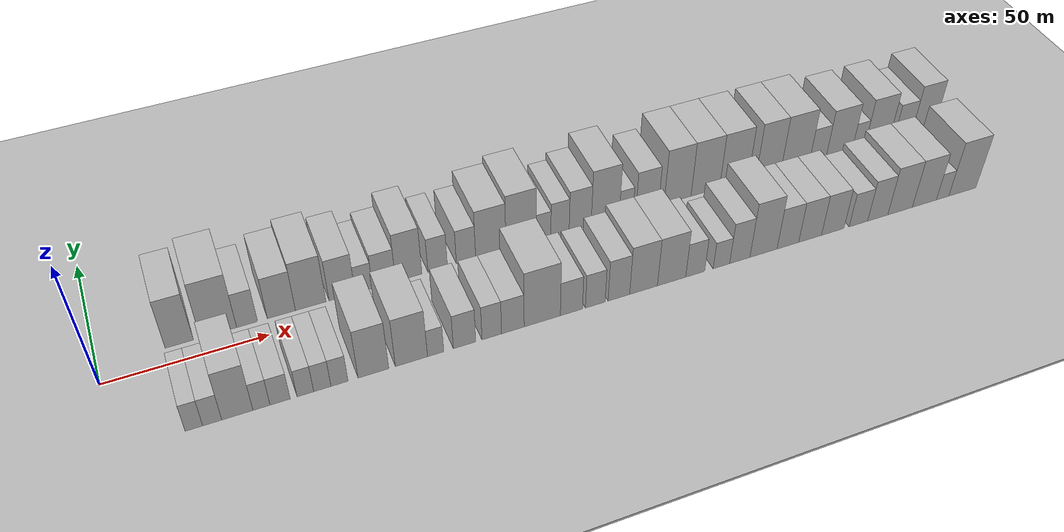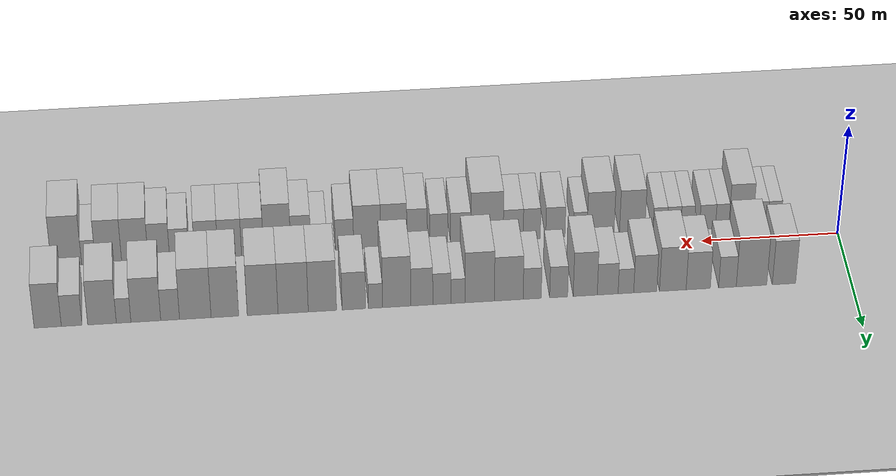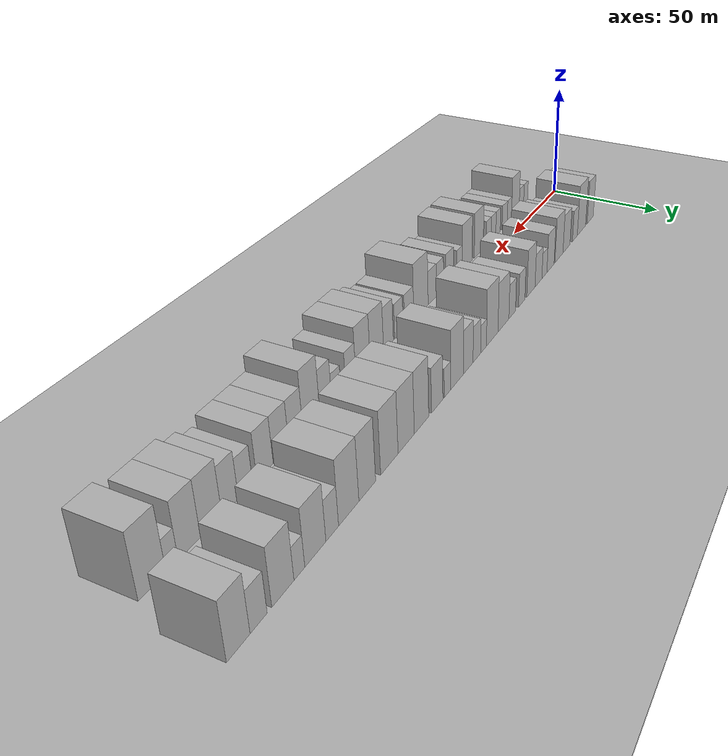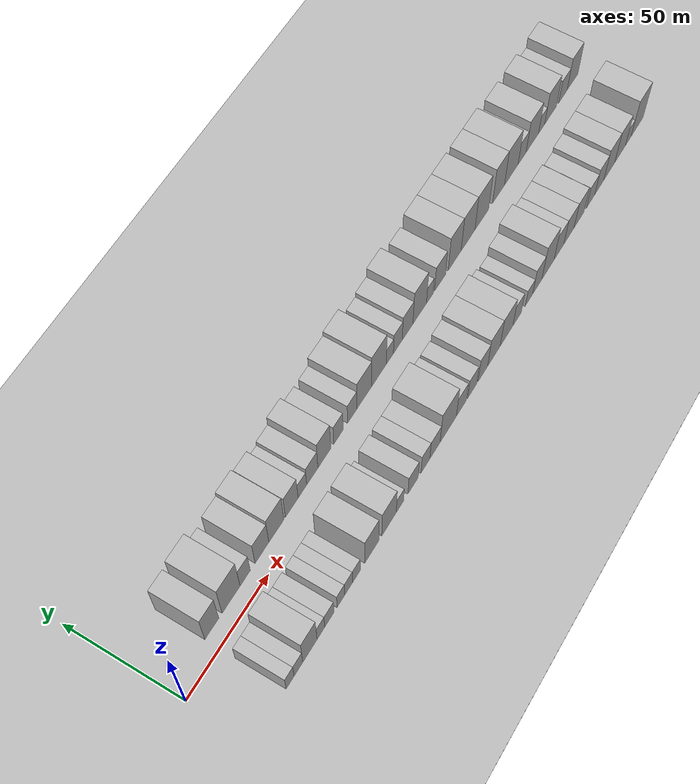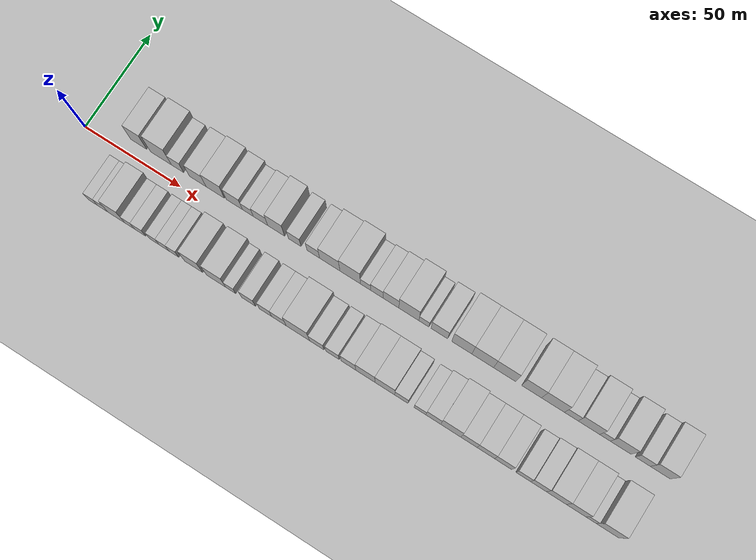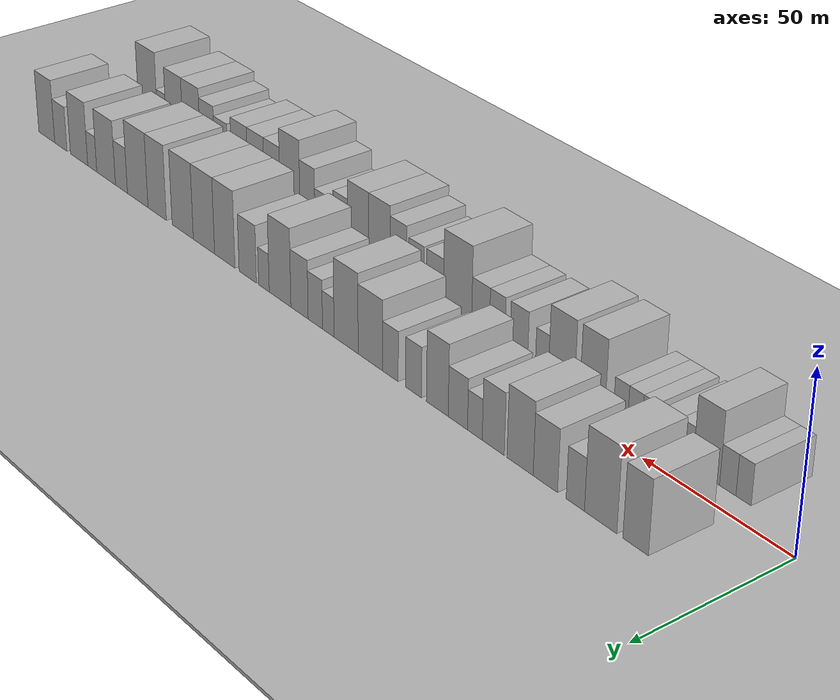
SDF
<?xml version="1.0" encoding="utf-8"?>

<sdf version="1.6">

   <world name="default">

      <gui fullscreen="0">

         <camera name="user_camera">

            <pose>-15 0 4.57585 0 0 0</pose>

            <view_controller>orbit</view_controller>

         </camera>

      </gui>

      <scene>

         <sky>

           <clouds>

             <speed>12</speed>

           </clouds>

         </sky>

         <ambient>0.4 0.4 0.4 1</ambient>

         <background>0.7 0.7 0.7 1</background>

         <shadows>1</shadows>

      </scene>

      <gravity>0 0 -9.8066</gravity>

      <magnetic_field>6e-06 2.3e-05 -4.2e-05</magnetic_field>

      <physics default="0" name="default_physics" type="ode">

         <ode>

            <solver>

               <type>quick</type>

               <iters>10</iters>

               <sor>1.0</sor>

               <use_dynamic_moi_rescaling>0</use_dynamic_moi_rescaling>

            </solver>

            <constraints>

               <cfm>0</cfm>

               <erp>0.2</erp>

               <contact_max_correcting_vel>100</contact_max_correcting_vel>

               <contact_surface_layer>0.001</contact_surface_layer>

            </constraints>

         </ode>

         <max_step_size>0.004</max_step_size>

         <real_time_factor>1</real_time_factor>

         <real_time_update_rate>250</real_time_update_rate>

      </physics>

      <light name="sun" type="directional">

         <cast_shadows>1</cast_shadows>

         <pose>0 0 10 0 0 0</pose>

         <diffuse>0.8 0.8 0.8 1</diffuse>

         <specular>0.2 0.2 0.2 1</specular>

         <attenuation>

            <range>1000</range>

            <constant>0.9</constant>

            <linear>0.01</linear>

            <quadratic>0.001</quadratic>

         </attenuation>

         <direction>-0.5 0.1 -0.9</direction>

      </light>

      <include>

         <name>ground_plane_1</name>

         <uri>model://HANNAS_ground_plane</uri>

         <pose>0 0 0  0 0 0</pose>

      </include>

      <include>

         <name>ground_plane_2</name>

         <uri>model://HANNAS_ground_plane</uri>

         <pose>100 0 0  0 0 0</pose>

      </include>

      <model name="building_1">

         <static>1</static>

         <pose frame="">24.2105 16.0000 0 0.000000 0.000000 1.570796</pose>

         <link name="link">

            <pose frame="">0 0 10.50 0 0 0</pose>

            <collision name="collision">

               <geometry>

                  <box>

                     <size>20.0000 8.4211 21.0000</size>

                  </box>

               </geometry>

               <max_contacts>10</max_contacts>

               <surface>

                  <contact>

                     <ode/>

                  </contact>

                  <bounce/>

                  <friction>

                     <torsional>

                        <ode/>

                     </torsional>

                     <ode/>

                  </friction>

               </surface>

            </collision>

            <visual name="visual">

               <cast_shadows>0</cast_shadows>

               <geometry>

                  <box>

                     <size>20.0000 8.4211 21.0000</size>

                  </box>

               </geometry>

               <material>

                  <script>

                     <uri>model://HANNAS_wall/materials/scripts</uri>

                     <uri>model://HANNAS_wall/materials/textures</uri>

                     <name>vrc/HANNAS_wall</name>

                  </script>

               </material>

            </visual>

            <self_collide>0</self_collide>

            <enable_wind>0</enable_wind>

            <kinematic>0</kinematic>

         </link>

      </model>

      <model name="building_2">

         <static>1</static>

         <pose frame="">35.9146 16.0000 0 0.000000 0.000000 1.570796</pose>

         <link name="link">

            <pose frame="">0 0 12.00 0 0 0</pose>

            <collision name="collision">

               <geometry>

                  <box>

                     <size>20.0000 10.9870 24.0000</size>

                  </box>

               </geometry>

               <max_contacts>10</max_contacts>

               <surface>

                  <contact>

                     <ode/>

                  </contact>

                  <bounce/>

                  <friction>

                     <torsional>

                        <ode/>

                     </torsional>

                     <ode/>

                  </friction>

               </surface>

            </collision>

            <visual name="visual">

               <cast_shadows>0</cast_shadows>

               <geometry>

                  <box>

                     <size>20.0000 10.9870 24.0000</size>

                  </box>

               </geometry>

               <material>

                  <script>

                     <uri>model://HANNAS_wall/materials/scripts</uri>

                     <uri>model://HANNAS_wall/materials/textures</uri>

                     <name>vrc/HANNAS_wall</name>

                  </script>

               </material>

            </visual>

            <self_collide>0</self_collide>

            <enable_wind>0</enable_wind>

            <kinematic>0</kinematic>

         </link>

      </model>

      <model name="building_3">

         <static>1</static>

         <pose frame="">44.5813 16.0000 0 0.000000 0.000000 1.570796</pose>

         <link name="link">

            <pose frame="">0 0 7.50 0 0 0</pose>

            <collision name="collision">

               <geometry>

                  <box>

                     <size>20.0000 6.3463 15.0000</size>

                  </box>

               </geometry>

               <max_contacts>10</max_contacts>

               <surface>

                  <contact>

                     <ode/>

                  </contact>

                  <bounce/>

                  <friction>

                     <torsional>

                        <ode/>

                     </torsional>

                     <ode/>

                  </friction>

               </surface>

            </collision>

            <visual name="visual">

               <cast_shadows>0</cast_shadows>

               <geometry>

                  <box>

                     <size>20.0000 6.3463 15.0000</size>

                  </box>

               </geometry>

               <material>

                  <script>

                     <uri>model://HANNAS_wall/materials/scripts</uri>

                     <uri>model://HANNAS_wall/materials/textures</uri>

                     <name>vrc/HANNAS_wall</name>

                  </script>

               </material>

            </visual>

            <self_collide>0</self_collide>

            <enable_wind>0</enable_wind>

            <kinematic>0</kinematic>

         </link>

      </model>

      <model name="building_4">

         <static>1</static>

         <pose frame="">55.1095 16.0000 0 0.000000 0.000000 1.570796</pose>

         <link name="link">

            <pose frame="">0 0 9.00 0 0 0</pose>

            <collision name="collision">

               <geometry>

                  <box>

                     <size>20.0000 8.7102 18.0000</size>

                  </box>

               </geometry>

               <max_contacts>10</max_contacts>

               <surface>

                  <contact>

                     <ode/>

                  </contact>

                  <bounce/>

                  <friction>

                     <torsional>

                        <ode/>

                     </torsional>

                     <ode/>

                  </friction>

               </surface>

            </collision>

            <visual name="visual">

               <cast_shadows>0</cast_shadows>

               <geometry>

                  <box>

                     <size>20.0000 8.7102 18.0000</size>

                  </box>

               </geometry>

               <material>

                  <script>

                     <uri>model://HANNAS_wall/materials/scripts</uri>

                     <uri>model://HANNAS_wall/materials/textures</uri>

                     <name>vrc/HANNAS_wall</name>

                  </script>

               </material>

            </visual>

            <self_collide>0</self_collide>

            <enable_wind>0</enable_wind>

            <kinematic>0</kinematic>

         </link>

      </model>

      <model name="building_5">

         <static>1</static>

         <pose frame="">64.2417 16.0000 0 0.000000 0.000000 1.570796</pose>

         <link name="link">

            <pose frame="">0 0 10.50 0 0 0</pose>

            <collision name="collision">

               <geometry>

                  <box>

                     <size>20.0000 9.5541 21.0000</size>

                  </box>

               </geometry>

               <max_contacts>10</max_contacts>

               <surface>

                  <contact>

                     <ode/>

                  </contact>

                  <bounce/>

                  <friction>

                     <torsional>

                        <ode/>

                     </torsional>

                     <ode/>

                  </friction>

               </surface>

            </collision>

            <visual name="visual">

               <cast_shadows>0</cast_shadows>

               <geometry>

                  <box>

                     <size>20.0000 9.5541 21.0000</size>

                  </box>

               </geometry>

               <material>

                  <script>

                     <uri>model://HANNAS_wall/materials/scripts</uri>

                     <uri>model://HANNAS_wall/materials/textures</uri>

                     <name>vrc/HANNAS_wall</name>

                  </script>

               </material>

            </visual>

            <self_collide>0</self_collide>

            <enable_wind>0</enable_wind>

            <kinematic>0</kinematic>

         </link>

      </model>

      <model name="building_6">

         <static>1</static>

         <pose frame="">74.1500 16.0000 0 0.000000 0.000000 1.570796</pose>

         <link name="link">

            <pose frame="">0 0 9.00 0 0 0</pose>

            <collision name="collision">

               <geometry>

                  <box>

                     <size>20.0000 8.2625 18.0000</size>

                  </box>

               </geometry>

               <max_contacts>10</max_contacts>

               <surface>

                  <contact>

                     <ode/>

                  </contact>

                  <bounce/>

                  <friction>

                     <torsional>

                        <ode/>

                     </torsional>

                     <ode/>

                  </friction>

               </surface>

            </collision>

            <visual name="visual">

               <cast_shadows>0</cast_shadows>

               <geometry>

                  <box>

                     <size>20.0000 8.2625 18.0000</size>

                  </box>

               </geometry>

               <material>

                  <script>

                     <uri>model://HANNAS_wall/materials/scripts</uri>

                     <uri>model://HANNAS_wall/materials/textures</uri>

                     <name>vrc/HANNAS_wall</name>

                  </script>

               </material>

            </visual>

            <self_collide>0</self_collide>

            <enable_wind>0</enable_wind>

            <kinematic>0</kinematic>

         </link>

      </model>

      <model name="building_7">

         <static>1</static>

         <pose frame="">81.0801 16.0000 0 0.000000 0.000000 1.570796</pose>

         <link name="link">

            <pose frame="">0 0 6.00 0 0 0</pose>

            <collision name="collision">

               <geometry>

                  <box>

                     <size>20.0000 5.5977 12.0000</size>

                  </box>

               </geometry>

               <max_contacts>10</max_contacts>

               <surface>

                  <contact>

                     <ode/>

                  </contact>

                  <bounce/>

                  <friction>

                     <torsional>

                        <ode/>

                     </torsional>

                     <ode/>

                  </friction>

               </surface>

            </collision>

            <visual name="visual">

               <cast_shadows>0</cast_shadows>

               <geometry>

                  <box>

                     <size>20.0000 5.5977 12.0000</size>

                  </box>

               </geometry>

               <material>

                  <script>

                     <uri>model://HANNAS_wall/materials/scripts</uri>

                     <uri>model://HANNAS_wall/materials/textures</uri>

                     <name>vrc/HANNAS_wall</name>

                  </script>

               </material>

            </visual>

            <self_collide>0</self_collide>

            <enable_wind>0</enable_wind>

            <kinematic>0</kinematic>

         </link>

      </model>

      <model name="building_8">

         <static>1</static>

         <pose frame="">87.6114 16.0000 0 0.000000 0.000000 1.570796</pose>

         <link name="link">

            <pose frame="">0 0 7.50 0 0 0</pose>

            <collision name="collision">

               <geometry>

                  <box>

                     <size>20.0000 7.4648 15.0000</size>

                  </box>

               </geometry>

               <max_contacts>10</max_contacts>

               <surface>

                  <contact>

                     <ode/>

                  </contact>

                  <bounce/>

                  <friction>

                     <torsional>

                        <ode/>

                     </torsional>

                     <ode/>

                  </friction>

               </surface>

            </collision>

            <visual name="visual">

               <cast_shadows>0</cast_shadows>

               <geometry>

                  <box>

                     <size>20.0000 7.4648 15.0000</size>

                  </box>

               </geometry>

               <material>

                  <script>

                     <uri>model://HANNAS_wall/materials/scripts</uri>

                     <uri>model://HANNAS_wall/materials/textures</uri>

                     <name>vrc/HANNAS_wall</name>

                  </script>

               </material>

            </visual>

            <self_collide>0</self_collide>

            <enable_wind>0</enable_wind>

            <kinematic>0</kinematic>

         </link>

      </model>

      <model name="building_9">

         <static>1</static>

         <pose frame="">95.6471 16.0000 0 0.000000 0.000000 1.570796</pose>

         <link name="link">

            <pose frame="">0 0 10.50 0 0 0</pose>

            <collision name="collision">

               <geometry>

                  <box>

                     <size>20.0000 8.6066 21.0000</size>

                  </box>

               </geometry>

               <max_contacts>10</max_contacts>

               <surface>

                  <contact>

                     <ode/>

                  </contact>

                  <bounce/>

                  <friction>

                     <torsional>

                        <ode/>

                     </torsional>

                     <ode/>

                  </friction>

               </surface>

            </collision>

            <visual name="visual">

               <cast_shadows>0</cast_shadows>

               <geometry>

                  <box>

                     <size>20.0000 8.6066 21.0000</size>

                  </box>

               </geometry>

               <material>

                  <script>

                     <uri>model://HANNAS_wall/materials/scripts</uri>

                     <uri>model://HANNAS_wall/materials/textures</uri>

                     <name>vrc/HANNAS_wall</name>

                  </script>

               </material>

            </visual>

            <self_collide>0</self_collide>

            <enable_wind>0</enable_wind>

            <kinematic>0</kinematic>

         </link>

      </model>

      <model name="building_10">

         <static>1</static>

         <pose frame="">105.1658 16.0000 0 0.000000 0.000000 1.570796</pose>

         <link name="link">

            <pose frame="">0 0 7.50 0 0 0</pose>

            <collision name="collision">

               <geometry>

                  <box>

                     <size>20.0000 6.4309 15.0000</size>

                  </box>

               </geometry>

               <max_contacts>10</max_contacts>

               <surface>

                  <contact>

                     <ode/>

                  </contact>

                  <bounce/>

                  <friction>

                     <torsional>

                        <ode/>

                     </torsional>

                     <ode/>

                  </friction>

               </surface>

            </collision>

            <visual name="visual">

               <cast_shadows>0</cast_shadows>

               <geometry>

                  <box>

                     <size>20.0000 6.4309 15.0000</size>

                  </box>

               </geometry>

               <material>

                  <script>

                     <uri>model://HANNAS_wall/materials/scripts</uri>

                     <uri>model://HANNAS_wall/materials/textures</uri>

                     <name>vrc/HANNAS_wall</name>

                  </script>

               </material>

            </visual>

            <self_collide>0</self_collide>

            <enable_wind>0</enable_wind>

            <kinematic>0</kinematic>

         </link>

      </model>

      <model name="building_11">

         <static>1</static>

         <pose frame="">114.6152 16.0000 0 0.000000 0.000000 1.570796</pose>

         <link name="link">

            <pose frame="">0 0 7.50 0 0 0</pose>

            <collision name="collision">

               <geometry>

                  <box>

                     <size>20.0000 6.4679 15.0000</size>

                  </box>

               </geometry>

               <max_contacts>10</max_contacts>

               <surface>

                  <contact>

                     <ode/>

                  </contact>

                  <bounce/>

                  <friction>

                     <torsional>

                        <ode/>

                     </torsional>

                     <ode/>

                  </friction>

               </surface>

            </collision>

            <visual name="visual">

               <cast_shadows>0</cast_shadows>

               <geometry>

                  <box>

                     <size>20.0000 6.4679 15.0000</size>

                  </box>

               </geometry>

               <material>

                  <script>

                     <uri>model://HANNAS_wall/materials/scripts</uri>

                     <uri>model://HANNAS_wall/materials/textures</uri>

                     <name>vrc/HANNAS_wall</name>

                  </script>

               </material>

            </visual>

            <self_collide>0</self_collide>

            <enable_wind>0</enable_wind>

            <kinematic>0</kinematic>

         </link>

      </model>

      <model name="building_12">

         <static>1</static>

         <pose frame="">122.9898 16.0000 0 0.000000 0.000000 1.570796</pose>

         <link name="link">

            <pose frame="">0 0 10.50 0 0 0</pose>

            <collision name="collision">

               <geometry>

                  <box>

                     <size>20.0000 10.2814 21.0000</size>

                  </box>

               </geometry>

               <max_contacts>10</max_contacts>

               <surface>

                  <contact>

                     <ode/>

                  </contact>

                  <bounce/>

                  <friction>

                     <torsional>

                        <ode/>

                     </torsional>

                     <ode/>

                  </friction>

               </surface>

            </collision>

            <visual name="visual">

               <cast_shadows>0</cast_shadows>

               <geometry>

                  <box>

                     <size>20.0000 10.2814 21.0000</size>

                  </box>

               </geometry>

               <material>

                  <script>

                     <uri>model://HANNAS_wall/materials/scripts</uri>

                     <uri>model://HANNAS_wall/materials/textures</uri>

                     <name>vrc/HANNAS_wall</name>

                  </script>

               </material>

            </visual>

            <self_collide>0</self_collide>

            <enable_wind>0</enable_wind>

            <kinematic>0</kinematic>

         </link>

      </model>

      <model name="building_13">

         <static>1</static>

         <pose frame="">133.3350 16.0000 0 0.000000 0.000000 1.570796</pose>

         <link name="link">

            <pose frame="">0 0 12.00 0 0 0</pose>

            <collision name="collision">

               <geometry>

                  <box>

                     <size>20.0000 10.4091 24.0000</size>

                  </box>

               </geometry>

               <max_contacts>10</max_contacts>

               <surface>

                  <contact>

                     <ode/>

                  </contact>

                  <bounce/>

                  <friction>

                     <torsional>

                        <ode/>

                     </torsional>

                     <ode/>

                  </friction>

               </surface>

            </collision>

            <visual name="visual">

               <cast_shadows>0</cast_shadows>

               <geometry>

                  <box>

                     <size>20.0000 10.4091 24.0000</size>

                  </box>

               </geometry>

               <material>

                  <script>

                     <uri>model://HANNAS_wall/materials/scripts</uri>

                     <uri>model://HANNAS_wall/materials/textures</uri>

                     <name>vrc/HANNAS_wall</name>

                  </script>

               </material>

            </visual>

            <self_collide>0</self_collide>

            <enable_wind>0</enable_wind>

            <kinematic>0</kinematic>

         </link>

      </model>

      <model name="building_14">

         <static>1</static>

         <pose frame="">141.0848 16.0000 0 0.000000 0.000000 1.570796</pose>

         <link name="link">

            <pose frame="">0 0 6.00 0 0 0</pose>

            <collision name="collision">

               <geometry>

                  <box>

                     <size>20.0000 5.0905 12.0000</size>

                  </box>

               </geometry>

               <max_contacts>10</max_contacts>

               <surface>

                  <contact>

                     <ode/>

                  </contact>

                  <bounce/>

                  <friction>

                     <torsional>

                        <ode/>

                     </torsional>

                     <ode/>

                  </friction>

               </surface>

            </collision>

            <visual name="visual">

               <cast_shadows>0</cast_shadows>

               <geometry>

                  <box>

                     <size>20.0000 5.0905 12.0000</size>

                  </box>

               </geometry>

               <material>

                  <script>

                     <uri>model://HANNAS_wall/materials/scripts</uri>

                     <uri>model://HANNAS_wall/materials/textures</uri>

                     <name>vrc/HANNAS_wall</name>

                  </script>

               </material>

            </visual>

            <self_collide>0</self_collide>

            <enable_wind>0</enable_wind>

            <kinematic>0</kinematic>

         </link>

      </model>

      <model name="building_15">

         <static>1</static>

         <pose frame="">146.8284 16.0000 0 0.000000 0.000000 1.570796</pose>

         <link name="link">

            <pose frame="">0 0 7.50 0 0 0</pose>

            <collision name="collision">

               <geometry>

                  <box>

                     <size>20.0000 6.3967 15.0000</size>

                  </box>

               </geometry>

               <max_contacts>10</max_contacts>

               <surface>

                  <contact>

                     <ode/>

                  </contact>

                  <bounce/>

                  <friction>

                     <torsional>

                        <ode/>

                     </torsional>

                     <ode/>

                  </friction>

               </surface>

            </collision>

            <visual name="visual">

               <cast_shadows>0</cast_shadows>

               <geometry>

                  <box>

                     <size>20.0000 6.3967 15.0000</size>

                  </box>

               </geometry>

               <material>

                  <script>

                     <uri>model://HANNAS_wall/materials/scripts</uri>

                     <uri>model://HANNAS_wall/materials/textures</uri>

                     <name>vrc/HANNAS_wall</name>

                  </script>

               </material>

            </visual>

            <self_collide>0</self_collide>

            <enable_wind>0</enable_wind>

            <kinematic>0</kinematic>

         </link>

      </model>

      <model name="building_16">

         <static>1</static>

         <pose frame="">153.9316 16.0000 0 0.000000 0.000000 1.570796</pose>

         <link name="link">

            <pose frame="">0 0 9.00 0 0 0</pose>

            <collision name="collision">

               <geometry>

                  <box>

                     <size>20.0000 7.8097 18.0000</size>

                  </box>

               </geometry>

               <max_contacts>10</max_contacts>

               <surface>

                  <contact>

                     <ode/>

                  </contact>

                  <bounce/>

                  <friction>

                     <torsional>

                        <ode/>

                     </torsional>

                     <ode/>

                  </friction>

               </surface>

            </collision>

            <visual name="visual">

               <cast_shadows>0</cast_shadows>

               <geometry>

                  <box>

                     <size>20.0000 7.8097 18.0000</size>

                  </box>

               </geometry>

               <material>

                  <script>

                     <uri>model://HANNAS_wall/materials/scripts</uri>

                     <uri>model://HANNAS_wall/materials/textures</uri>

                     <name>vrc/HANNAS_wall</name>

                  </script>

               </material>

            </visual>

            <self_collide>0</self_collide>

            <enable_wind>0</enable_wind>

            <kinematic>0</kinematic>

         </link>

      </model>

      <model name="building_17">

         <static>1</static>

         <pose frame="">162.8556 16.0000 0 0.000000 0.000000 1.570796</pose>

         <link name="link">

            <pose frame="">0 0 12.00 0 0 0</pose>

            <collision name="collision">

               <geometry>

                  <box>

                     <size>20.0000 10.0382 24.0000</size>

                  </box>

               </geometry>

               <max_contacts>10</max_contacts>

               <surface>

                  <contact>

                     <ode/>

                  </contact>

                  <bounce/>

                  <friction>

                     <torsional>

                        <ode/>

                     </torsional>

                     <ode/>

                  </friction>

               </surface>

            </collision>

            <visual name="visual">

               <cast_shadows>0</cast_shadows>

               <geometry>

                  <box>

                     <size>20.0000 10.0382 24.0000</size>

                  </box>

               </geometry>

               <material>

                  <script>

                     <uri>model://HANNAS_wall/materials/scripts</uri>

                     <uri>model://HANNAS_wall/materials/textures</uri>

                     <name>vrc/HANNAS_wall</name>

                  </script>

               </material>

            </visual>

            <self_collide>0</self_collide>

            <enable_wind>0</enable_wind>

            <kinematic>0</kinematic>

         </link>

      </model>

      <model name="building_18">

         <static>1</static>

         <pose frame="">170.3821 16.0000 0 0.000000 0.000000 1.570796</pose>

         <link name="link">

            <pose frame="">0 0 6.00 0 0 0</pose>

            <collision name="collision">

               <geometry>

                  <box>

                     <size>20.0000 5.0147 12.0000</size>

                  </box>

               </geometry>

               <max_contacts>10</max_contacts>

               <surface>

                  <contact>

                     <ode/>

                  </contact>

                  <bounce/>

                  <friction>

                     <torsional>

                        <ode/>

                     </torsional>

                     <ode/>

                  </friction>

               </surface>

            </collision>

            <visual name="visual">

               <cast_shadows>0</cast_shadows>

               <geometry>

                  <box>

                     <size>20.0000 5.0147 12.0000</size>

                  </box>

               </geometry>

               <material>

                  <script>

                     <uri>model://HANNAS_wall/materials/scripts</uri>

                     <uri>model://HANNAS_wall/materials/textures</uri>

                     <name>vrc/HANNAS_wall</name>

                  </script>

               </material>

            </visual>

            <self_collide>0</self_collide>

            <enable_wind>0</enable_wind>

            <kinematic>0</kinematic>

         </link>

      </model>

      <model name="building_19">

         <static>1</static>

         <pose frame="">178.0471 16.0000 0 0.000000 0.000000 1.570796</pose>

         <link name="link">

            <pose frame="">0 0 9.00 0 0 0</pose>

            <collision name="collision">

               <geometry>

                  <box>

                     <size>20.0000 8.3153 18.0000</size>

                  </box>

               </geometry>

               <max_contacts>10</max_contacts>

               <surface>

                  <contact>

                     <ode/>

                  </contact>

                  <bounce/>

                  <friction>

                     <torsional>

                        <ode/>

                     </torsional>

                     <ode/>

                  </friction>

               </surface>

            </collision>

            <visual name="visual">

               <cast_shadows>0</cast_shadows>

               <geometry>

                  <box>

                     <size>20.0000 8.3153 18.0000</size>

                  </box>

               </geometry>

               <material>

                  <script>

                     <uri>model://HANNAS_wall/materials/scripts</uri>

                     <uri>model://HANNAS_wall/materials/textures</uri>

                     <name>vrc/HANNAS_wall</name>

                  </script>

               </material>

            </visual>

            <self_collide>0</self_collide>

            <enable_wind>0</enable_wind>

            <kinematic>0</kinematic>

         </link>

      </model>

      <model name="building_20">

         <static>1</static>

         <pose frame="">189.2018 16.0000 0 0.000000 0.000000 1.570796</pose>

         <link name="link">

            <pose frame="">0 0 12.00 0 0 0</pose>

            <collision name="collision">

               <geometry>

                  <box>

                     <size>20.0000 9.9940 24.0000</size>

                  </box>

               </geometry>

               <max_contacts>10</max_contacts>

               <surface>

                  <contact>

                     <ode/>

                  </contact>

                  <bounce/>

                  <friction>

                     <torsional>

                        <ode/>

                     </torsional>

                     <ode/>

                  </friction>

               </surface>

            </collision>

            <visual name="visual">

               <cast_shadows>0</cast_shadows>

               <geometry>

                  <box>

                     <size>20.0000 9.9940 24.0000</size>

                  </box>

               </geometry>

               <material>

                  <script>

                     <uri>model://HANNAS_wall/materials/scripts</uri>

                     <uri>model://HANNAS_wall/materials/textures</uri>

                     <name>vrc/HANNAS_wall</name>

                  </script>

               </material>

            </visual>

            <self_collide>0</self_collide>

            <enable_wind>0</enable_wind>

            <kinematic>0</kinematic>

         </link>

      </model>

      <model name="building_21">

         <static>1</static>

         <pose frame="">199.5516 16.0000 0 0.000000 0.000000 1.570796</pose>

         <link name="link">

            <pose frame="">0 0 12.00 0 0 0</pose>

            <collision name="collision">

               <geometry>

                  <box>

                     <size>20.0000 10.7056 24.0000</size>

                  </box>

               </geometry>

               <max_contacts>10</max_contacts>

               <surface>

                  <contact>

                     <ode/>

                  </contact>

                  <bounce/>

                  <friction>

                     <torsional>

                        <ode/>

                     </torsional>

                     <ode/>

                  </friction>

               </surface>

            </collision>

            <visual name="visual">

               <cast_shadows>0</cast_shadows>

               <geometry>

                  <box>

                     <size>20.0000 10.7056 24.0000</size>

                  </box>

               </geometry>

               <material>

                  <script>

                     <uri>model://HANNAS_wall/materials/scripts</uri>

                     <uri>model://HANNAS_wall/materials/textures</uri>

                     <name>vrc/HANNAS_wall</name>

                  </script>

               </material>

            </visual>

            <self_collide>0</self_collide>

            <enable_wind>0</enable_wind>

            <kinematic>0</kinematic>

         </link>

      </model>

      <model name="building_22">

         <static>1</static>

         <pose frame="">210.3530 16.0000 0 0.000000 0.000000 1.570796</pose>

         <link name="link">

            <pose frame="">0 0 12.00 0 0 0</pose>

            <collision name="collision">

               <geometry>

                  <box>

                     <size>20.0000 10.8971 24.0000</size>

                  </box>

               </geometry>

               <max_contacts>10</max_contacts>

               <surface>

                  <contact>

                     <ode/>

                  </contact>

                  <bounce/>

                  <friction>

                     <torsional>

                        <ode/>

                     </torsional>

                     <ode/>

                  </friction>

               </surface>

            </collision>

            <visual name="visual">

               <cast_shadows>0</cast_shadows>

               <geometry>

                  <box>

                     <size>20.0000 10.8971 24.0000</size>

                  </box>

               </geometry>

               <material>

                  <script>

                     <uri>model://HANNAS_wall/materials/scripts</uri>

                     <uri>model://HANNAS_wall/materials/textures</uri>

                     <name>vrc/HANNAS_wall</name>

                  </script>

               </material>

            </visual>

            <self_collide>0</self_collide>

            <enable_wind>0</enable_wind>

            <kinematic>0</kinematic>

         </link>

      </model>

      <model name="building_23">

         <static>1</static>

         <pose frame="">223.6579 16.0000 0 0.000000 0.000000 1.570796</pose>

         <link name="link">

            <pose frame="">0 0 12.00 0 0 0</pose>

            <collision name="collision">

               <geometry>

                  <box>

                     <size>20.0000 9.7128 24.0000</size>

                  </box>

               </geometry>

               <max_contacts>10</max_contacts>

               <surface>

                  <contact>

                     <ode/>

                  </contact>

                  <bounce/>

                  <friction>

                     <torsional>

                        <ode/>

                     </torsional>

                     <ode/>

                  </friction>

               </surface>

            </collision>

            <visual name="visual">

               <cast_shadows>0</cast_shadows>

               <geometry>

                  <box>

                     <size>20.0000 9.7128 24.0000</size>

                  </box>

               </geometry>

               <material>

                  <script>

                     <uri>model://HANNAS_wall/materials/scripts</uri>

                     <uri>model://HANNAS_wall/materials/textures</uri>

                     <name>vrc/HANNAS_wall</name>

                  </script>

               </material>

            </visual>

            <self_collide>0</self_collide>

            <enable_wind>0</enable_wind>

            <kinematic>0</kinematic>

         </link>

      </model>

      <model name="building_24">

         <static>1</static>

         <pose frame="">234.0782 16.0000 0 0.000000 0.000000 1.570796</pose>

         <link name="link">

            <pose frame="">0 0 12.00 0 0 0</pose>

            <collision name="collision">

               <geometry>

                  <box>

                     <size>20.0000 11.1277 24.0000</size>

                  </box>

               </geometry>

               <max_contacts>10</max_contacts>

               <surface>

                  <contact>

                     <ode/>

                  </contact>

                  <bounce/>

                  <friction>

                     <torsional>

                        <ode/>

                     </torsional>

                     <ode/>

                  </friction>

               </surface>

            </collision>

            <visual name="visual">

               <cast_shadows>0</cast_shadows>

               <geometry>

                  <box>

                     <size>20.0000 11.1277 24.0000</size>

                  </box>

               </geometry>

               <material>

                  <script>

                     <uri>model://HANNAS_wall/materials/scripts</uri>

                     <uri>model://HANNAS_wall/materials/textures</uri>

                     <name>vrc/HANNAS_wall</name>

                  </script>

               </material>

            </visual>

            <self_collide>0</self_collide>

            <enable_wind>0</enable_wind>

            <kinematic>0</kinematic>

         </link>

      </model>

      <model name="building_25">

         <static>1</static>

         <pose frame="">242.9531 16.0000 0 0.000000 0.000000 1.570796</pose>

         <link name="link">

            <pose frame="">0 0 7.50 0 0 0</pose>

            <collision name="collision">

               <geometry>

                  <box>

                     <size>20.0000 6.6221 15.0000</size>

                  </box>

               </geometry>

               <max_contacts>10</max_contacts>

               <surface>

                  <contact>

                     <ode/>

                  </contact>

                  <bounce/>

                  <friction>

                     <torsional>

                        <ode/>

                     </torsional>

                     <ode/>

                  </friction>

               </surface>

            </collision>

            <visual name="visual">

               <cast_shadows>0</cast_shadows>

               <geometry>

                  <box>

                     <size>20.0000 6.6221 15.0000</size>

                  </box>

               </geometry>

               <material>

                  <script>

                     <uri>model://HANNAS_wall/materials/scripts</uri>

                     <uri>model://HANNAS_wall/materials/textures</uri>

                     <name>vrc/HANNAS_wall</name>

                  </script>

               </material>

            </visual>

            <self_collide>0</self_collide>

            <enable_wind>0</enable_wind>

            <kinematic>0</kinematic>

         </link>

      </model>

      <model name="building_26">

         <static>1</static>

         <pose frame="">251.5019 16.0000 0 0.000000 0.000000 1.570796</pose>

         <link name="link">

            <pose frame="">0 0 10.50 0 0 0</pose>

            <collision name="collision">

               <geometry>

                  <box>

                     <size>20.0000 10.4754 21.0000</size>

                  </box>

               </geometry>

               <max_contacts>10</max_contacts>

               <surface>

                  <contact>

                     <ode/>

                  </contact>

                  <bounce/>

                  <friction>

                     <torsional>

                        <ode/>

                     </torsional>

                     <ode/>

                  </friction>

               </surface>

            </collision>

            <visual name="visual">

               <cast_shadows>0</cast_shadows>

               <geometry>

                  <box>

                     <size>20.0000 10.4754 21.0000</size>

                  </box>

               </geometry>

               <material>

                  <script>

                     <uri>model://HANNAS_wall/materials/scripts</uri>

                     <uri>model://HANNAS_wall/materials/textures</uri>

                     <name>vrc/HANNAS_wall</name>

                  </script>

               </material>

            </visual>

            <self_collide>0</self_collide>

            <enable_wind>0</enable_wind>

            <kinematic>0</kinematic>

         </link>

      </model>

      <model name="building_27">

         <static>1</static>

         <pose frame="">259.3025 16.0000 0 0.000000 0.000000 1.570796</pose>

         <link name="link">

            <pose frame="">0 0 6.00 0 0 0</pose>

            <collision name="collision">

               <geometry>

                  <box>

                     <size>20.0000 5.1259 12.0000</size>

                  </box>

               </geometry>

               <max_contacts>10</max_contacts>

               <surface>

                  <contact>

                     <ode/>

                  </contact>

                  <bounce/>

                  <friction>

                     <torsional>

                        <ode/>

                     </torsional>

                     <ode/>

                  </friction>

               </surface>

            </collision>

            <visual name="visual">

               <cast_shadows>0</cast_shadows>

               <geometry>

                  <box>

                     <size>20.0000 5.1259 12.0000</size>

                  </box>

               </geometry>

               <material>

                  <script>

                     <uri>model://HANNAS_wall/materials/scripts</uri>

                     <uri>model://HANNAS_wall/materials/textures</uri>

                     <name>vrc/HANNAS_wall</name>

                  </script>

               </material>

            </visual>

            <self_collide>0</self_collide>

            <enable_wind>0</enable_wind>

            <kinematic>0</kinematic>

         </link>

      </model>

      <model name="building_28">

         <static>1</static>

         <pose frame="">266.8906 16.0000 0 0.000000 0.000000 1.570796</pose>

         <link name="link">

            <pose frame="">0 0 10.50 0 0 0</pose>

            <collision name="collision">

               <geometry>

                  <box>

                     <size>20.0000 10.0502 21.0000</size>

                  </box>

               </geometry>

               <max_contacts>10</max_contacts>

               <surface>

                  <contact>

                     <ode/>

                  </contact>

                  <bounce/>

                  <friction>

                     <torsional>

                        <ode/>

                     </torsional>

                     <ode/>

                  </friction>

               </surface>

            </collision>

            <visual name="visual">

               <cast_shadows>0</cast_shadows>

               <geometry>

                  <box>

                     <size>20.0000 10.0502 21.0000</size>

                  </box>

               </geometry>

               <material>

                  <script>

                     <uri>model://HANNAS_wall/materials/scripts</uri>

                     <uri>model://HANNAS_wall/materials/textures</uri>

                     <name>vrc/HANNAS_wall</name>

                  </script>

               </material>

            </visual>

            <self_collide>0</self_collide>

            <enable_wind>0</enable_wind>

            <kinematic>0</kinematic>

         </link>

      </model>

      <model name="building_29">

         <static>1</static>

         <pose frame="">277.5307 16.0000 0 0.000000 0.000000 1.570796</pose>

         <link name="link">

            <pose frame="">0 0 7.50 0 0 0</pose>

            <collision name="collision">

               <geometry>

                  <box>

                     <size>20.0000 7.2301 15.0000</size>

                  </box>

               </geometry>

               <max_contacts>10</max_contacts>

               <surface>

                  <contact>

                     <ode/>

                  </contact>

                  <bounce/>

                  <friction>

                     <torsional>

                        <ode/>

                     </torsional>

                     <ode/>

                  </friction>

               </surface>

            </collision>

            <visual name="visual">

               <cast_shadows>0</cast_shadows>

               <geometry>

                  <box>

                     <size>20.0000 7.2301 15.0000</size>

                  </box>

               </geometry>

               <material>

                  <script>

                     <uri>model://HANNAS_wall/materials/scripts</uri>

                     <uri>model://HANNAS_wall/materials/textures</uri>

                     <name>vrc/HANNAS_wall</name>

                  </script>

               </material>

            </visual>

            <self_collide>0</self_collide>

            <enable_wind>0</enable_wind>

            <kinematic>0</kinematic>

         </link>

      </model>

      <model name="building_30">

         <static>1</static>

         <pose frame="">285.9117 16.0000 0 0.000000 0.000000 1.570796</pose>

         <link name="link">

            <pose frame="">0 0 10.50 0 0 0</pose>

            <collision name="collision">

               <geometry>

                  <box>

                     <size>20.0000 9.5318 21.0000</size>

                  </box>

               </geometry>

               <max_contacts>10</max_contacts>

               <surface>

                  <contact>

                     <ode/>

                  </contact>

                  <bounce/>

                  <friction>

                     <torsional>

                        <ode/>

                     </torsional>

                     <ode/>

                  </friction>

               </surface>

            </collision>

            <visual name="visual">

               <cast_shadows>0</cast_shadows>

               <geometry>

                  <box>

                     <size>20.0000 9.5318 21.0000</size>

                  </box>

               </geometry>

               <material>

                  <script>

                     <uri>model://HANNAS_wall/materials/scripts</uri>

                     <uri>model://HANNAS_wall/materials/textures</uri>

                     <name>vrc/HANNAS_wall</name>

                  </script>

               </material>

            </visual>

            <self_collide>0</self_collide>

            <enable_wind>0</enable_wind>

            <kinematic>0</kinematic>

         </link>

      </model>

      <model name="building_31">

         <static>1</static>

         <pose frame="">22.4566 -16.0000 0 0.000000 0.000000 1.570796</pose>

         <link name="link">

            <pose frame="">0 0 6.00 0 0 0</pose>

            <collision name="collision">

               <geometry>

                  <box>

                     <size>20.0000 4.9133 12.0000</size>

                  </box>

               </geometry>

               <max_contacts>10</max_contacts>

               <surface>

                  <contact>

                     <ode/>

                  </contact>

                  <bounce/>

                  <friction>

                     <torsional>

                        <ode/>

                     </torsional>

                     <ode/>

                  </friction>

               </surface>

            </collision>

            <visual name="visual">

               <cast_shadows>0</cast_shadows>

               <geometry>

                  <box>

                     <size>20.0000 4.9133 12.0000</size>

                  </box>

               </geometry>

               <material>

                  <script>

                     <uri>model://HANNAS_wall/materials/scripts</uri>

                     <uri>model://HANNAS_wall/materials/textures</uri>

                     <name>vrc/HANNAS_wall</name>

                  </script>

               </material>

            </visual>

            <self_collide>0</self_collide>

            <enable_wind>0</enable_wind>

            <kinematic>0</kinematic>

         </link>

      </model>

      <model name="building_32">

         <static>1</static>

         <pose frame="">27.5971 -16.0000 0 0.000000 0.000000 1.570796</pose>

         <link name="link">

            <pose frame="">0 0 6.00 0 0 0</pose>

            <collision name="collision">

               <geometry>

                  <box>

                     <size>20.0000 5.3676 12.0000</size>

                  </box>

               </geometry>

               <max_contacts>10</max_contacts>

               <surface>

                  <contact>

                     <ode/>

                  </contact>

                  <bounce/>

                  <friction>

                     <torsional>

                        <ode/>

                     </torsional>

                     <ode/>

                  </friction>

               </surface>

            </collision>

            <visual name="visual">

               <cast_shadows>0</cast_shadows>

               <geometry>

                  <box>

                     <size>20.0000 5.3676 12.0000</size>

                  </box>

               </geometry>

               <material>

                  <script>

                     <uri>model://HANNAS_wall/materials/scripts</uri>

                     <uri>model://HANNAS_wall/materials/textures</uri>

                     <name>vrc/HANNAS_wall</name>

                  </script>

               </material>

            </visual>

            <self_collide>0</self_collide>

            <enable_wind>0</enable_wind>

            <kinematic>0</kinematic>

         </link>

      </model>

      <model name="building_33">

         <static>1</static>

         <pose frame="">34.7237 -16.0000 0 0.000000 0.000000 1.570796</pose>

         <link name="link">

            <pose frame="">0 0 10.50 0 0 0</pose>

            <collision name="collision">

               <geometry>

                  <box>

                     <size>20.0000 8.8856 21.0000</size>

                  </box>

               </geometry>

               <max_contacts>10</max_contacts>

               <surface>

                  <contact>

                     <ode/>

                  </contact>

                  <bounce/>

                  <friction>

                     <torsional>

                        <ode/>

                     </torsional>

                     <ode/>

                  </friction>

               </surface>

            </collision>

            <visual name="visual">

               <cast_shadows>0</cast_shadows>

               <geometry>

                  <box>

                     <size>20.0000 8.8856 21.0000</size>

                  </box>

               </geometry>

               <material>

                  <script>

                     <uri>model://HANNAS_wall/materials/scripts</uri>

                     <uri>model://HANNAS_wall/materials/textures</uri>

                     <name>vrc/HANNAS_wall</name>

                  </script>

               </material>

            </visual>

            <self_collide>0</self_collide>

            <enable_wind>0</enable_wind>

            <kinematic>0</kinematic>

         </link>

      </model>

      <model name="building_34">

         <static>1</static>

         <pose frame="">41.6181 -16.0000 0 0.000000 0.000000 1.570796</pose>

         <link name="link">

            <pose frame="">0 0 6.00 0 0 0</pose>

            <collision name="collision">

               <geometry>

                  <box>

                     <size>20.0000 4.9032 12.0000</size>

                  </box>

               </geometry>

               <max_contacts>10</max_contacts>

               <surface>

                  <contact>

                     <ode/>

                  </contact>

                  <bounce/>

                  <friction>

                     <torsional>

                        <ode/>

                     </torsional>

                     <ode/>

                  </friction>

               </surface>

            </collision>

            <visual name="visual">

               <cast_shadows>0</cast_shadows>

               <geometry>

                  <box>

                     <size>20.0000 4.9032 12.0000</size>

                  </box>

               </geometry>

               <material>

                  <script>

                     <uri>model://HANNAS_wall/materials/scripts</uri>

                     <uri>model://HANNAS_wall/materials/textures</uri>

                     <name>vrc/HANNAS_wall</name>

                  </script>

               </material>

            </visual>

            <self_collide>0</self_collide>

            <enable_wind>0</enable_wind>

            <kinematic>0</kinematic>

         </link>

      </model>

      <model name="building_35">

         <static>1</static>

         <pose frame="">46.9980 -16.0000 0 0.000000 0.000000 1.570796</pose>

         <link name="link">

            <pose frame="">0 0 6.00 0 0 0</pose>

            <collision name="collision">

               <geometry>

                  <box>

                     <size>20.0000 5.8566 12.0000</size>

                  </box>

               </geometry>

               <max_contacts>10</max_contacts>

               <surface>

                  <contact>

                     <ode/>

                  </contact>

                  <bounce/>

                  <friction>

                     <torsional>

                        <ode/>

                     </torsional>

                     <ode/>

                  </friction>

               </surface>

            </collision>

            <visual name="visual">

               <cast_shadows>0</cast_shadows>

               <geometry>

                  <box>

                     <size>20.0000 5.8566 12.0000</size>

                  </box>

               </geometry>

               <material>

                  <script>

                     <uri>model://HANNAS_wall/materials/scripts</uri>

                     <uri>model://HANNAS_wall/materials/textures</uri>

                     <name>vrc/HANNAS_wall</name>

                  </script>

               </material>

            </visual>

            <self_collide>0</self_collide>

            <enable_wind>0</enable_wind>

            <kinematic>0</kinematic>

         </link>

      </model>

      <model name="building_36">

         <static>1</static>

         <pose frame="">54.3711 -16.0000 0 0.000000 0.000000 1.570796</pose>

         <link name="link">

            <pose frame="">0 0 6.00 0 0 0</pose>

            <collision name="collision">

               <geometry>

                  <box>

                     <size>20.0000 4.8896 12.0000</size>

                  </box>

               </geometry>

               <max_contacts>10</max_contacts>

               <surface>

                  <contact>

                     <ode/>

                  </contact>

                  <bounce/>

                  <friction>

                     <torsional>

                        <ode/>

                     </torsional>

                     <ode/>

                  </friction>

               </surface>

            </collision>

            <visual name="visual">

               <cast_shadows>0</cast_shadows>

               <geometry>

                  <box>

                     <size>20.0000 4.8896 12.0000</size>

                  </box>

               </geometry>

               <material>

                  <script>

                     <uri>model://HANNAS_wall/materials/scripts</uri>

                     <uri>model://HANNAS_wall/materials/textures</uri>

                     <name>vrc/HANNAS_wall</name>

                  </script>

               </material>

            </visual>

            <self_collide>0</self_collide>

            <enable_wind>0</enable_wind>

            <kinematic>0</kinematic>

         </link>

      </model>

      <model name="building_37">

         <static>1</static>

         <pose frame="">59.3655 -16.0000 0 0.000000 0.000000 1.570796</pose>

         <link name="link">

            <pose frame="">0 0 6.00 0 0 0</pose>

            <collision name="collision">

               <geometry>

                  <box>

                     <size>20.0000 5.0992 12.0000</size>

                  </box>

               </geometry>

               <max_contacts>10</max_contacts>

               <surface>

                  <contact>

                     <ode/>

                  </contact>

                  <bounce/>

                  <friction>

                     <torsional>

                        <ode/>

                     </torsional>

                     <ode/>

                  </friction>

               </surface>

            </collision>

            <visual name="visual">

               <cast_shadows>0</cast_shadows>

               <geometry>

                  <box>

                     <size>20.0000 5.0992 12.0000</size>

                  </box>

               </geometry>

               <material>

                  <script>

                     <uri>model://HANNAS_wall/materials/scripts</uri>

                     <uri>model://HANNAS_wall/materials/textures</uri>

                     <name>vrc/HANNAS_wall</name>

                  </script>

               </material>

            </visual>

            <self_collide>0</self_collide>

            <enable_wind>0</enable_wind>

            <kinematic>0</kinematic>

         </link>

      </model>

      <model name="building_38">

         <static>1</static>

         <pose frame="">64.4580 -16.0000 0 0.000000 0.000000 1.570796</pose>

         <link name="link">

            <pose frame="">0 0 6.00 0 0 0</pose>

            <collision name="collision">

               <geometry>

                  <box>

                     <size>20.0000 5.0858 12.0000</size>

                  </box>

               </geometry>

               <max_contacts>10</max_contacts>

               <surface>

                  <contact>

                     <ode/>

                  </contact>

                  <bounce/>

                  <friction>

                     <torsional>

                        <ode/>

                     </torsional>

                     <ode/>

                  </friction>

               </surface>

            </collision>

            <visual name="visual">

               <cast_shadows>0</cast_shadows>

               <geometry>

                  <box>

                     <size>20.0000 5.0858 12.0000</size>

                  </box>

               </geometry>

               <material>

                  <script>

                     <uri>model://HANNAS_wall/materials/scripts</uri>

                     <uri>model://HANNAS_wall/materials/textures</uri>

                     <name>vrc/HANNAS_wall</name>

                  </script>

               </material>

            </visual>

            <self_collide>0</self_collide>

            <enable_wind>0</enable_wind>

            <kinematic>0</kinematic>

         </link>

      </model>

      <model name="building_39">

         <static>1</static>

         <pose frame="">74.6477 -16.0000 0 0.000000 0.000000 1.570796</pose>

         <link name="link">

            <pose frame="">0 0 10.50 0 0 0</pose>

            <collision name="collision">

               <geometry>

                  <box>

                     <size>20.0000 9.2937 21.0000</size>

                  </box>

               </geometry>

               <max_contacts>10</max_contacts>

               <surface>

                  <contact>

                     <ode/>

                  </contact>

                  <bounce/>

                  <friction>

                     <torsional>

                        <ode/>

                     </torsional>

                     <ode/>

                  </friction>

               </surface>

            </collision>

            <visual name="visual">

               <cast_shadows>0</cast_shadows>

               <geometry>

                  <box>

                     <size>20.0000 9.2937 21.0000</size>

                  </box>

               </geometry>

               <material>

                  <script>

                     <uri>model://HANNAS_wall/materials/scripts</uri>

                     <uri>model://HANNAS_wall/materials/textures</uri>

                     <name>vrc/HANNAS_wall</name>

                  </script>

               </material>

            </visual>

            <self_collide>0</self_collide>

            <enable_wind>0</enable_wind>

            <kinematic>0</kinematic>

         </link>

      </model>

      <model name="building_40">

         <static>1</static>

         <pose frame="">86.2326 -16.0000 0 0.000000 0.000000 1.570796</pose>

         <link name="link">

            <pose frame="">0 0 10.50 0 0 0</pose>

            <collision name="collision">

               <geometry>

                  <box>

                     <size>20.0000 9.8760 21.0000</size>

                  </box>

               </geometry>

               <max_contacts>10</max_contacts>

               <surface>

                  <contact>

                     <ode/>

                  </contact>

                  <bounce/>

                  <friction>

                     <torsional>

                        <ode/>

                     </torsional>

                     <ode/>

                  </friction>

               </surface>

            </collision>

            <visual name="visual">

               <cast_shadows>0</cast_shadows>

               <geometry>

                  <box>

                     <size>20.0000 9.8760 21.0000</size>

                  </box>

               </geometry>

               <material>

                  <script>

                     <uri>model://HANNAS_wall/materials/scripts</uri>

                     <uri>model://HANNAS_wall/materials/textures</uri>

                     <name>vrc/HANNAS_wall</name>

                  </script>

               </material>

            </visual>

            <self_collide>0</self_collide>

            <enable_wind>0</enable_wind>

            <kinematic>0</kinematic>

         </link>

      </model>

      <model name="building_41">

         <static>1</static>

         <pose frame="">93.6965 -16.0000 0 0.000000 0.000000 1.570796</pose>

         <link name="link">

            <pose frame="">0 0 6.00 0 0 0</pose>

            <collision name="collision">

               <geometry>

                  <box>

                     <size>20.0000 5.0519 12.0000</size>

                  </box>

               </geometry>

               <max_contacts>10</max_contacts>

               <surface>

                  <contact>

                     <ode/>

                  </contact>

                  <bounce/>

                  <friction>

                     <torsional>

                        <ode/>

                     </torsional>

                     <ode/>

                  </friction>

               </surface>

            </collision>

            <visual name="visual">

               <cast_shadows>0</cast_shadows>

               <geometry>

                  <box>

                     <size>20.0000 5.0519 12.0000</size>

                  </box>

               </geometry>

               <material>

                  <script>

                     <uri>model://HANNAS_wall/materials/scripts</uri>

                     <uri>model://HANNAS_wall/materials/textures</uri>

                     <name>vrc/HANNAS_wall</name>

                  </script>

               </material>

            </visual>

            <self_collide>0</self_collide>

            <enable_wind>0</enable_wind>

            <kinematic>0</kinematic>

         </link>

      </model>

      <model name="building_42">

         <static>1</static>

         <pose frame="">102.7391 -16.0000 0 0.000000 0.000000 1.570796</pose>

         <link name="link">

            <pose frame="">0 0 7.50 0 0 0</pose>

            <collision name="collision">

               <geometry>

                  <box>

                     <size>20.0000 7.0334 15.0000</size>

                  </box>

               </geometry>

               <max_contacts>10</max_contacts>

               <surface>

                  <contact>

                     <ode/>

                  </contact>

                  <bounce/>

                  <friction>

                     <torsional>

                        <ode/>

                     </torsional>

                     <ode/>

                  </friction>

               </surface>

            </collision>

            <visual name="visual">

               <cast_shadows>0</cast_shadows>

               <geometry>

                  <box>

                     <size>20.0000 7.0334 15.0000</size>

                  </box>

               </geometry>

               <material>

                  <script>

                     <uri>model://HANNAS_wall/materials/scripts</uri>

                     <uri>model://HANNAS_wall/materials/textures</uri>

                     <name>vrc/HANNAS_wall</name>

                  </script>

               </material>

            </visual>

            <self_collide>0</self_collide>

            <enable_wind>0</enable_wind>

            <kinematic>0</kinematic>

         </link>

      </model>

      <model name="building_43">

         <static>1</static>

         <pose frame="">111.3708 -16.0000 0 0.000000 0.000000 1.570796</pose>

         <link name="link">

            <pose frame="">0 0 7.50 0 0 0</pose>

            <collision name="collision">

               <geometry>

                  <box>

                     <size>20.0000 6.2300 15.0000</size>

                  </box>

               </geometry>

               <max_contacts>10</max_contacts>

               <surface>

                  <contact>

                     <ode/>

                  </contact>

                  <bounce/>

                  <friction>

                     <torsional>

                        <ode/>

                     </torsional>

                     <ode/>

                  </friction>

               </surface>

            </collision>

            <visual name="visual">

               <cast_shadows>0</cast_shadows>

               <geometry>

                  <box>

                     <size>20.0000 6.2300 15.0000</size>

                  </box>

               </geometry>

               <material>

                  <script>

                     <uri>model://HANNAS_wall/materials/scripts</uri>

                     <uri>model://HANNAS_wall/materials/textures</uri>

                     <name>vrc/HANNAS_wall</name>

                  </script>

               </material>

            </visual>

            <self_collide>0</self_collide>

            <enable_wind>0</enable_wind>

            <kinematic>0</kinematic>

         </link>

      </model>

      <model name="building_44">

         <static>1</static>

         <pose frame="">118.1234 -16.0000 0 0.000000 0.000000 1.570796</pose>

         <link name="link">

            <pose frame="">0 0 7.50 0 0 0</pose>

            <collision name="collision">

               <geometry>

                  <box>

                     <size>20.0000 7.2752 15.0000</size>

                  </box>

               </geometry>

               <max_contacts>10</max_contacts>

               <surface>

                  <contact>

                     <ode/>

                  </contact>

                  <bounce/>

                  <friction>

                     <torsional>

                        <ode/>

                     </torsional>

                     <ode/>

                  </friction>

               </surface>

            </collision>

            <visual name="visual">

               <cast_shadows>0</cast_shadows>

               <geometry>

                  <box>

                     <size>20.0000 7.2752 15.0000</size>

                  </box>

               </geometry>

               <material>

                  <script>

                     <uri>model://HANNAS_wall/materials/scripts</uri>

                     <uri>model://HANNAS_wall/materials/textures</uri>

                     <name>vrc/HANNAS_wall</name>

                  </script>

               </material>

            </visual>

            <self_collide>0</self_collide>

            <enable_wind>0</enable_wind>

            <kinematic>0</kinematic>

         </link>

      </model>

      <model name="building_45">

         <static>1</static>

         <pose frame="">127.6679 -16.0000 0 0.000000 0.000000 1.570796</pose>

         <link name="link">

            <pose frame="">0 0 12.00 0 0 0</pose>

            <collision name="collision">

               <geometry>

                  <box>

                     <size>20.0000 11.8139 24.0000</size>

                  </box>

               </geometry>

               <max_contacts>10</max_contacts>

               <surface>

                  <contact>

                     <ode/>

                  </contact>

                  <bounce/>

                  <friction>

                     <torsional>

                        <ode/>

                     </torsional>

                     <ode/>

                  </friction>

               </surface>

            </collision>

            <visual name="visual">

               <cast_shadows>0</cast_shadows>

               <geometry>

                  <box>

                     <size>20.0000 11.8139 24.0000</size>

                  </box>

               </geometry>

               <material>

                  <script>

                     <uri>model://HANNAS_wall/materials/scripts</uri>

                     <uri>model://HANNAS_wall/materials/textures</uri>

                     <name>vrc/HANNAS_wall</name>

                  </script>

               </material>

            </visual>

            <self_collide>0</self_collide>

            <enable_wind>0</enable_wind>

            <kinematic>0</kinematic>

         </link>

      </model>

      <model name="building_46">

         <static>1</static>

         <pose frame="">137.2229 -16.0000 0 0.000000 0.000000 1.570796</pose>

         <link name="link">

            <pose frame="">0 0 7.50 0 0 0</pose>

            <collision name="collision">

               <geometry>

                  <box>

                     <size>20.0000 7.2961 15.0000</size>

                  </box>

               </geometry>

               <max_contacts>10</max_contacts>

               <surface>

                  <contact>

                     <ode/>

                  </contact>

                  <bounce/>

                  <friction>

                     <torsional>

                        <ode/>

                     </torsional>

                     <ode/>

                  </friction>

               </surface>

            </collision>

            <visual name="visual">

               <cast_shadows>0</cast_shadows>

               <geometry>

                  <box>

                     <size>20.0000 7.2961 15.0000</size>

                  </box>

               </geometry>

               <material>

                  <script>

                     <uri>model://HANNAS_wall/materials/scripts</uri>

                     <uri>model://HANNAS_wall/materials/textures</uri>

                     <name>vrc/HANNAS_wall</name>

                  </script>

               </material>

            </visual>

            <self_collide>0</self_collide>

            <enable_wind>0</enable_wind>

            <kinematic>0</kinematic>

         </link>

      </model>

      <model name="building_47">

         <static>1</static>

         <pose frame="">145.1562 -16.0000 0 0.000000 0.000000 1.570796</pose>

         <link name="link">

            <pose frame="">0 0 7.50 0 0 0</pose>

            <collision name="collision">

               <geometry>

                  <box>

                     <size>20.0000 6.5704 15.0000</size>

                  </box>

               </geometry>

               <max_contacts>10</max_contacts>

               <surface>

                  <contact>

                     <ode/>

                  </contact>

                  <bounce/>

                  <friction>

                     <torsional>

                        <ode/>

                     </torsional>

                     <ode/>

                  </friction>

               </surface>

            </collision>

            <visual name="visual">

               <cast_shadows>0</cast_shadows>

               <geometry>

                  <box>

                     <size>20.0000 6.5704 15.0000</size>

                  </box>

               </geometry>

               <material>

                  <script>

                     <uri>model://HANNAS_wall/materials/scripts</uri>

                     <uri>model://HANNAS_wall/materials/textures</uri>

                     <name>vrc/HANNAS_wall</name>

                  </script>

               </material>

            </visual>

            <self_collide>0</self_collide>

            <enable_wind>0</enable_wind>

            <kinematic>0</kinematic>

         </link>

      </model>

      <model name="building_48">

         <static>1</static>

         <pose frame="">153.0912 -16.0000 0 0.000000 0.000000 1.570796</pose>

         <link name="link">

            <pose frame="">0 0 9.00 0 0 0</pose>

            <collision name="collision">

               <geometry>

                  <box>

                     <size>20.0000 7.2997 18.0000</size>

                  </box>

               </geometry>

               <max_contacts>10</max_contacts>

               <surface>

                  <contact>

                     <ode/>

                  </contact>

                  <bounce/>

                  <friction>

                     <torsional>

                        <ode/>

                     </torsional>

                     <ode/>

                  </friction>

               </surface>

            </collision>

            <visual name="visual">

               <cast_shadows>0</cast_shadows>

               <geometry>

                  <box>

                     <size>20.0000 7.2997 18.0000</size>

                  </box>

               </geometry>

               <material>

                  <script>

                     <uri>model://HANNAS_wall/materials/scripts</uri>

                     <uri>model://HANNAS_wall/materials/textures</uri>

                     <name>vrc/HANNAS_wall</name>

                  </script>

               </material>

            </visual>

            <self_collide>0</self_collide>

            <enable_wind>0</enable_wind>

            <kinematic>0</kinematic>

         </link>

      </model>

      <model name="building_49">

         <static>1</static>

         <pose frame="">161.4949 -16.0000 0 0.000000 0.000000 1.570796</pose>

         <link name="link">

            <pose frame="">0 0 10.50 0 0 0</pose>

            <collision name="collision">

               <geometry>

                  <box>

                     <size>20.0000 9.5077 21.0000</size>

                  </box>

               </geometry>

               <max_contacts>10</max_contacts>

               <surface>

                  <contact>

                     <ode/>

                  </contact>

                  <bounce/>

                  <friction>

                     <torsional>

                        <ode/>

                     </torsional>

                     <ode/>

                  </friction>

               </surface>

            </collision>

            <visual name="visual">

               <cast_shadows>0</cast_shadows>

               <geometry>

                  <box>

                     <size>20.0000 9.5077 21.0000</size>

                  </box>

               </geometry>

               <material>

                  <script>

                     <uri>model://HANNAS_wall/materials/scripts</uri>

                     <uri>model://HANNAS_wall/materials/textures</uri>

                     <name>vrc/HANNAS_wall</name>

                  </script>

               </material>

            </visual>

            <self_collide>0</self_collide>

            <enable_wind>0</enable_wind>

            <kinematic>0</kinematic>

         </link>

      </model>

      <model name="building_50">

         <static>1</static>

         <pose frame="">171.1492 -16.0000 0 0.000000 0.000000 1.570796</pose>

         <link name="link">

            <pose frame="">0 0 10.50 0 0 0</pose>

            <collision name="collision">

               <geometry>

                  <box>

                     <size>20.0000 9.8008 21.0000</size>

                  </box>

               </geometry>

               <max_contacts>10</max_contacts>

               <surface>

                  <contact>

                     <ode/>

                  </contact>

                  <bounce/>

                  <friction>

                     <torsional>

                        <ode/>

                     </torsional>

                     <ode/>

                  </friction>

               </surface>

            </collision>

            <visual name="visual">

               <cast_shadows>0</cast_shadows>

               <geometry>

                  <box>

                     <size>20.0000 9.8008 21.0000</size>

                  </box>

               </geometry>

               <material>

                  <script>

                     <uri>model://HANNAS_wall/materials/scripts</uri>

                     <uri>model://HANNAS_wall/materials/textures</uri>

                     <name>vrc/HANNAS_wall</name>

                  </script>

               </material>

            </visual>

            <self_collide>0</self_collide>

            <enable_wind>0</enable_wind>

            <kinematic>0</kinematic>

         </link>

      </model>

      <model name="building_51">

         <static>1</static>

         <pose frame="">179.3652 -16.0000 0 0.000000 0.000000 1.570796</pose>

         <link name="link">

            <pose frame="">0 0 7.50 0 0 0</pose>

            <collision name="collision">

               <geometry>

                  <box>

                     <size>20.0000 6.6311 15.0000</size>

                  </box>

               </geometry>

               <max_contacts>10</max_contacts>

               <surface>

                  <contact>

                     <ode/>

                  </contact>

                  <bounce/>

                  <friction>

                     <torsional>

                        <ode/>

                     </torsional>

                     <ode/>

                  </friction>

               </surface>

            </collision>

            <visual name="visual">

               <cast_shadows>0</cast_shadows>

               <geometry>

                  <box>

                     <size>20.0000 6.6311 15.0000</size>

                  </box>

               </geometry>

               <material>

                  <script>

                     <uri>model://HANNAS_wall/materials/scripts</uri>

                     <uri>model://HANNAS_wall/materials/textures</uri>

                     <name>vrc/HANNAS_wall</name>

                  </script>

               </material>

            </visual>

            <self_collide>0</self_collide>

            <enable_wind>0</enable_wind>

            <kinematic>0</kinematic>

         </link>

      </model>

      <model name="building_52">

         <static>1</static>

         <pose frame="">188.6065 -16.0000 0 0.000000 0.000000 1.570796</pose>

         <link name="link">

            <pose frame="">0 0 6.00 0 0 0</pose>

            <collision name="collision">

               <geometry>

                  <box>

                     <size>20.0000 5.8515 12.0000</size>

                  </box>

               </geometry>

               <max_contacts>10</max_contacts>

               <surface>

                  <contact>

                     <ode/>

                  </contact>

                  <bounce/>

                  <friction>

                     <torsional>

                        <ode/>

                     </torsional>

                     <ode/>

                  </friction>

               </surface>

            </collision>

            <visual name="visual">

               <cast_shadows>0</cast_shadows>

               <geometry>

                  <box>

                     <size>20.0000 5.8515 12.0000</size>

                  </box>

               </geometry>

               <material>

                  <script>

                     <uri>model://HANNAS_wall/materials/scripts</uri>

                     <uri>model://HANNAS_wall/materials/textures</uri>

                     <name>vrc/HANNAS_wall</name>

                  </script>

               </material>

            </visual>

            <self_collide>0</self_collide>

            <enable_wind>0</enable_wind>

            <kinematic>0</kinematic>

         </link>

      </model>

      <model name="building_53">

         <static>1</static>

         <pose frame="">195.1559 -16.0000 0 0.000000 0.000000 1.570796</pose>

         <link name="link">

            <pose frame="">0 0 9.00 0 0 0</pose>

            <collision name="collision">

               <geometry>

                  <box>

                     <size>20.0000 7.2474 18.0000</size>

                  </box>

               </geometry>

               <max_contacts>10</max_contacts>

               <surface>

                  <contact>

                     <ode/>

                  </contact>

                  <bounce/>

                  <friction>

                     <torsional>

                        <ode/>

                     </torsional>

                     <ode/>

                  </friction>

               </surface>

            </collision>

            <visual name="visual">

               <cast_shadows>0</cast_shadows>

               <geometry>

                  <box>

                     <size>20.0000 7.2474 18.0000</size>

                  </box>

               </geometry>

               <material>

                  <script>

                     <uri>model://HANNAS_wall/materials/scripts</uri>

                     <uri>model://HANNAS_wall/materials/textures</uri>

                     <name>vrc/HANNAS_wall</name>

                  </script>

               </material>

            </visual>

            <self_collide>0</self_collide>

            <enable_wind>0</enable_wind>

            <kinematic>0</kinematic>

         </link>

      </model>

      <model name="building_54">

         <static>1</static>

         <pose frame="">203.7086 -16.0000 0 0.000000 0.000000 1.570796</pose>

         <link name="link">

            <pose frame="">0 0 12.00 0 0 0</pose>

            <collision name="collision">

               <geometry>

                  <box>

                     <size>20.0000 9.8580 24.0000</size>

                  </box>

               </geometry>

               <max_contacts>10</max_contacts>

               <surface>

                  <contact>

                     <ode/>

                  </contact>

                  <bounce/>

                  <friction>

                     <torsional>

                        <ode/>

                     </torsional>

                     <ode/>

                  </friction>

               </surface>

            </collision>

            <visual name="visual">

               <cast_shadows>0</cast_shadows>

               <geometry>

                  <box>

                     <size>20.0000 9.8580 24.0000</size>

                  </box>

               </geometry>

               <material>

                  <script>

                     <uri>model://HANNAS_wall/materials/scripts</uri>

                     <uri>model://HANNAS_wall/materials/textures</uri>

                     <name>vrc/HANNAS_wall</name>

                  </script>

               </material>

            </visual>

            <self_collide>0</self_collide>

            <enable_wind>0</enable_wind>

            <kinematic>0</kinematic>

         </link>

      </model>

      <model name="building_55">

         <static>1</static>

         <pose frame="">212.5999 -16.0000 0 0.000000 0.000000 1.570796</pose>

         <link name="link">

            <pose frame="">0 0 9.00 0 0 0</pose>

            <collision name="collision">

               <geometry>

                  <box>

                     <size>20.0000 7.9246 18.0000</size>

                  </box>

               </geometry>

               <max_contacts>10</max_contacts>

               <surface>

                  <contact>

                     <ode/>

                  </contact>

                  <bounce/>

                  <friction>

                     <torsional>

                        <ode/>

                     </torsional>

                     <ode/>

                  </friction>

               </surface>

            </collision>

            <visual name="visual">

               <cast_shadows>0</cast_shadows>

               <geometry>

                  <box>

                     <size>20.0000 7.9246 18.0000</size>

                  </box>

               </geometry>

               <material>

                  <script>

                     <uri>model://HANNAS_wall/materials/scripts</uri>

                     <uri>model://HANNAS_wall/materials/textures</uri>

                     <name>vrc/HANNAS_wall</name>

                  </script>

               </material>

            </visual>

            <self_collide>0</self_collide>

            <enable_wind>0</enable_wind>

            <kinematic>0</kinematic>

         </link>

      </model>

      <model name="building_56">

         <static>1</static>

         <pose frame="">220.8051 -16.0000 0 0.000000 0.000000 1.570796</pose>

         <link name="link">

            <pose frame="">0 0 9.00 0 0 0</pose>

            <collision name="collision">

               <geometry>

                  <box>

                     <size>20.0000 8.4857 18.0000</size>

                  </box>

               </geometry>

               <max_contacts>10</max_contacts>

               <surface>

                  <contact>

                     <ode/>

                  </contact>

                  <bounce/>

                  <friction>

                     <torsional>

                        <ode/>

                     </torsional>

                     <ode/>

                  </friction>

               </surface>

            </collision>

            <visual name="visual">

               <cast_shadows>0</cast_shadows>

               <geometry>

                  <box>

                     <size>20.0000 8.4857 18.0000</size>

                  </box>

               </geometry>

               <material>

                  <script>

                     <uri>model://HANNAS_wall/materials/scripts</uri>

                     <uri>model://HANNAS_wall/materials/textures</uri>

                     <name>vrc/HANNAS_wall</name>

                  </script>

               </material>

            </visual>

            <self_collide>0</self_collide>

            <enable_wind>0</enable_wind>

            <kinematic>0</kinematic>

         </link>

      </model>

      <model name="building_57">

         <static>1</static>

         <pose frame="">229.2428 -16.0000 0 0.000000 0.000000 1.570796</pose>

         <link name="link">

            <pose frame="">0 0 9.00 0 0 0</pose>

            <collision name="collision">

               <geometry>

                  <box>

                     <size>20.0000 8.3898 18.0000</size>

                  </box>

               </geometry>

               <max_contacts>10</max_contacts>

               <surface>

                  <contact>

                     <ode/>

                  </contact>

                  <bounce/>

                  <friction>

                     <torsional>

                        <ode/>

                     </torsional>

                     <ode/>

                  </friction>

               </surface>

            </collision>

            <visual name="visual">

               <cast_shadows>0</cast_shadows>

               <geometry>

                  <box>

                     <size>20.0000 8.3898 18.0000</size>

                  </box>

               </geometry>

               <material>

                  <script>

                     <uri>model://HANNAS_wall/materials/scripts</uri>

                     <uri>model://HANNAS_wall/materials/textures</uri>

                     <name>vrc/HANNAS_wall</name>

                  </script>

               </material>

            </visual>

            <self_collide>0</self_collide>

            <enable_wind>0</enable_wind>

            <kinematic>0</kinematic>

         </link>

      </model>

      <model name="building_58">

         <static>1</static>

         <pose frame="">238.9333 -16.0000 0 0.000000 0.000000 1.570796</pose>

         <link name="link">

            <pose frame="">0 0 7.50 0 0 0</pose>

            <collision name="collision">

               <geometry>

                  <box>

                     <size>20.0000 6.9911 15.0000</size>

                  </box>

               </geometry>

               <max_contacts>10</max_contacts>

               <surface>

                  <contact>

                     <ode/>

                  </contact>

                  <bounce/>

                  <friction>

                     <torsional>

                        <ode/>

                     </torsional>

                     <ode/>

                  </friction>

               </surface>

            </collision>

            <visual name="visual">

               <cast_shadows>0</cast_shadows>

               <geometry>

                  <box>

                     <size>20.0000 6.9911 15.0000</size>

                  </box>

               </geometry>

               <material>

                  <script>

                     <uri>model://HANNAS_wall/materials/scripts</uri>

                     <uri>model://HANNAS_wall/materials/textures</uri>

                     <name>vrc/HANNAS_wall</name>

                  </script>

               </material>

            </visual>

            <self_collide>0</self_collide>

            <enable_wind>0</enable_wind>

            <kinematic>0</kinematic>

         </link>

      </model>

      <model name="building_59">

         <static>1</static>

         <pose frame="">246.2877 -16.0000 0 0.000000 0.000000 1.570796</pose>

         <link name="link">

            <pose frame="">0 0 9.00 0 0 0</pose>

            <collision name="collision">

               <geometry>

                  <box>

                     <size>20.0000 7.7177 18.0000</size>

                  </box>

               </geometry>

               <max_contacts>10</max_contacts>

               <surface>

                  <contact>

                     <ode/>

                  </contact>

                  <bounce/>

                  <friction>

                     <torsional>

                        <ode/>

                     </torsional>

                     <ode/>

                  </friction>

               </surface>

            </collision>

            <visual name="visual">

               <cast_shadows>0</cast_shadows>

               <geometry>

                  <box>

                     <size>20.0000 7.7177 18.0000</size>

                  </box>

               </geometry>

               <material>

                  <script>

                     <uri>model://HANNAS_wall/materials/scripts</uri>

                     <uri>model://HANNAS_wall/materials/textures</uri>

                     <name>vrc/HANNAS_wall</name>

                  </script>

               </material>

            </visual>

            <self_collide>0</self_collide>

            <enable_wind>0</enable_wind>

            <kinematic>0</kinematic>

         </link>

      </model>

      <model name="building_60">

         <static>1</static>

         <pose frame="">254.9115 -16.0000 0 0.000000 0.000000 1.570796</pose>

         <link name="link">

            <pose frame="">0 0 10.50 0 0 0</pose>

            <collision name="collision">

               <geometry>

                  <box>

                     <size>20.0000 9.5301 21.0000</size>

                  </box>

               </geometry>

               <max_contacts>10</max_contacts>

               <surface>

                  <contact>

                     <ode/>

                  </contact>

                  <bounce/>

                  <friction>

                     <torsional>

                        <ode/>

                     </torsional>

                     <ode/>

                  </friction>

               </surface>

            </collision>

            <visual name="visual">

               <cast_shadows>0</cast_shadows>

               <geometry>

                  <box>

                     <size>20.0000 9.5301 21.0000</size>

                  </box>

               </geometry>

               <material>

                  <script>

                     <uri>model://HANNAS_wall/materials/scripts</uri>

                     <uri>model://HANNAS_wall/materials/textures</uri>

                     <name>vrc/HANNAS_wall</name>

                  </script>

               </material>

            </visual>

            <self_collide>0</self_collide>

            <enable_wind>0</enable_wind>

            <kinematic>0</kinematic>

         </link>

      </model>

      <model name="building_61">

         <static>1</static>

         <pose frame="">264.3810 -16.0000 0 0.000000 0.000000 1.570796</pose>

         <link name="link">

            <pose frame="">0 0 10.50 0 0 0</pose>

            <collision name="collision">

               <geometry>

                  <box>

                     <size>20.0000 9.4089 21.0000</size>

                  </box>

               </geometry>

               <max_contacts>10</max_contacts>

               <surface>

                  <contact>

                     <ode/>

                  </contact>

                  <bounce/>

                  <friction>

                     <torsional>

                        <ode/>

                     </torsional>

                     <ode/>

                  </friction>

               </surface>

            </collision>

            <visual name="visual">

               <cast_shadows>0</cast_shadows>

               <geometry>

                  <box>

                     <size>20.0000 9.4089 21.0000</size>

                  </box>

               </geometry>

               <material>

                  <script>

                     <uri>model://HANNAS_wall/materials/scripts</uri>

                     <uri>model://HANNAS_wall/materials/textures</uri>

                     <name>vrc/HANNAS_wall</name>

                  </script>

               </material>

            </visual>

            <self_collide>0</self_collide>

            <enable_wind>0</enable_wind>

            <kinematic>0</kinematic>

         </link>

      </model>

      <model name="building_62">

         <static>1</static>

         <pose frame="">271.5593 -16.0000 0 0.000000 0.000000 1.570796</pose>

         <link name="link">

            <pose frame="">0 0 6.00 0 0 0</pose>

            <collision name="collision">

               <geometry>

                  <box>

                     <size>20.0000 4.9477 12.0000</size>

                  </box>

               </geometry>

               <max_contacts>10</max_contacts>

               <surface>

                  <contact>

                     <ode/>

                  </contact>

                  <bounce/>

                  <friction>

                     <torsional>

                        <ode/>

                     </torsional>

                     <ode/>

                  </friction>

               </surface>

            </collision>

            <visual name="visual">

               <cast_shadows>0</cast_shadows>

               <geometry>

                  <box>

                     <size>20.0000 4.9477 12.0000</size>

                  </box>

               </geometry>

               <material>

                  <script>

                     <uri>model://HANNAS_wall/materials/scripts</uri>

                     <uri>model://HANNAS_wall/materials/textures</uri>

                     <name>vrc/HANNAS_wall</name>

                  </script>

               </material>

            </visual>

            <self_collide>0</self_collide>

            <enable_wind>0</enable_wind>

            <kinematic>0</kinematic>

         </link>

      </model>

      <model name="building_63">

         <static>1</static>

         <pose frame="">279.4418 -16.0000 0 0.000000 0.000000 1.570796</pose>

         <link name="link">

            <pose frame="">0 0 12.00 0 0 0</pose>

            <collision name="collision">

               <geometry>

                  <box>

                     <size>20.0000 10.8171 24.0000</size>

                  </box>

               </geometry>

               <max_contacts>10</max_contacts>

               <surface>

                  <contact>

                     <ode/>

                  </contact>

                  <bounce/>

                  <friction>

                     <torsional>

                        <ode/>

                     </torsional>

                     <ode/>

                  </friction>

               </surface>

            </collision>

            <visual name="visual">

               <cast_shadows>0</cast_shadows>

               <geometry>

                  <box>

                     <size>20.0000 10.8171 24.0000</size>

                  </box>

               </geometry>

               <material>

                  <script>

                     <uri>model://HANNAS_wall/materials/scripts</uri>

                     <uri>model://HANNAS_wall/materials/textures</uri>

                     <name>vrc/HANNAS_wall</name>

                  </script>

               </material>

            </visual>

            <self_collide>0</self_collide>

            <enable_wind>0</enable_wind>

            <kinematic>0</kinematic>

         </link>

      </model>

   </world>

</sdf>

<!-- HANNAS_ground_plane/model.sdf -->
<sdf version="1.4">
<model name="HANNAS_ground_plane">
  <static>true</static>
    <link name="link">
      <collision name="collision">
        <geometry>
          <plane>
            <normal>0 0 1</normal>
            <size>1000 1000</size>
          </plane>
        </geometry>
        <surface>
          <friction>
            <ode>
              <mu>100</mu>
              <mu2>50</mu2>
            </ode>
          </friction>
        </surface>
      </collision>
      <visual name="visual">
        <cast_shadows>false</cast_shadows>
        <geometry>
          <plane>
            <normal>0 0 1</normal>
            <size>1000 1000</size>
          </plane>
        </geometry>
        <material>
          <script>
            <uri>model://HANNAS_ground_plane/materials/scripts/HANNAS_ground_plane.material</uri>
	    <uri>model://HANNAS_ground_plane/materials/textures</uri>
            <name>HANNASGroundPlane/Image</name>
          </script>
        </material>
      </visual>
    </link>
  </model>
</sdf>
